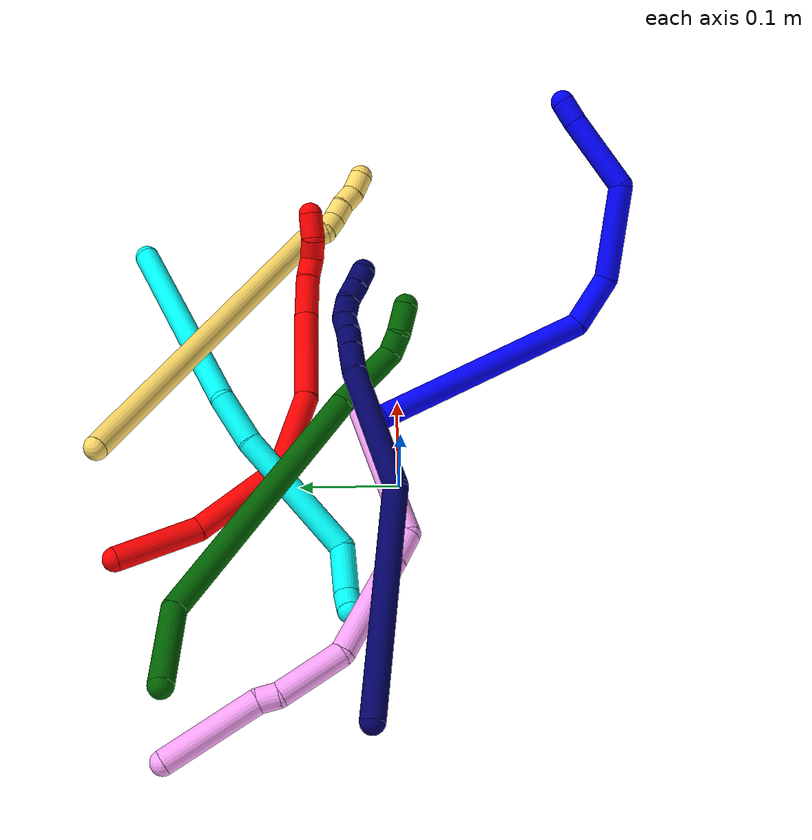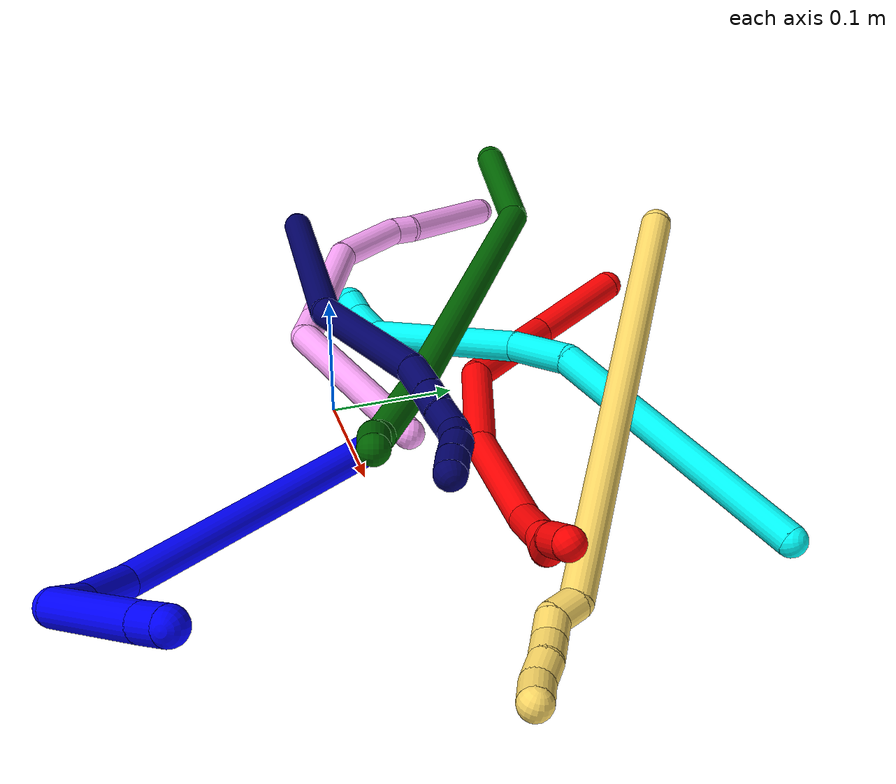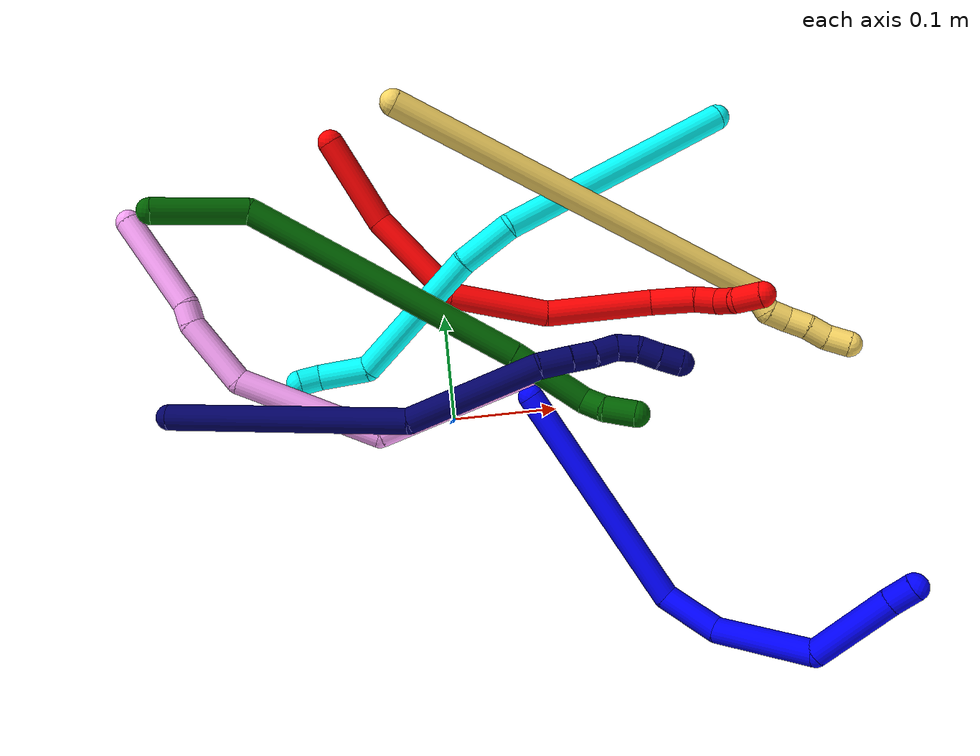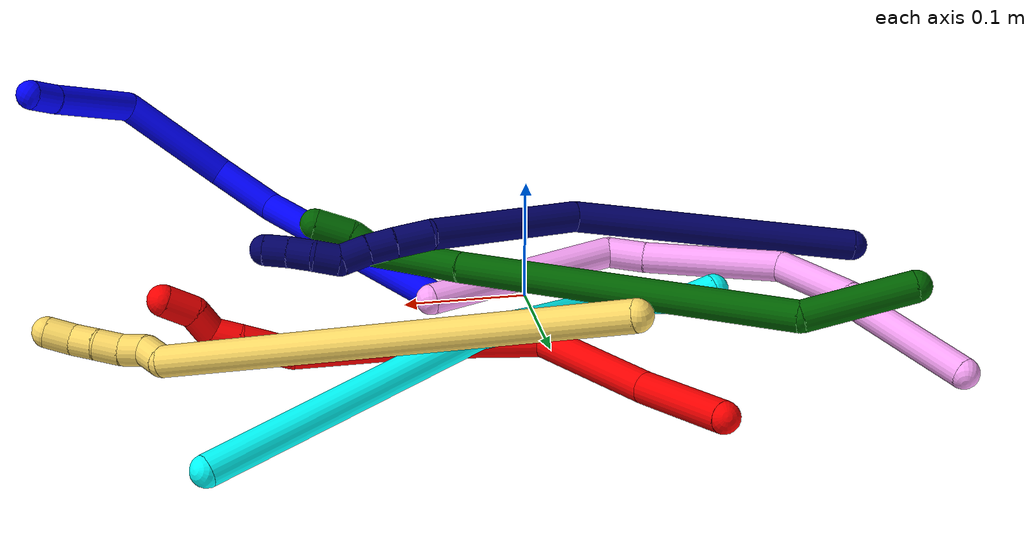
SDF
<sdf version="1.7">
 <world name="default">
  <plugin name="TubeGeneratorPlugin" filename="libtube_generator_plugin.so"/>
  <model name="photoneo_s_sensor">
   <static>1</static>
   <pose>0 0 2 1.57079 1.57079 3.14159</pose>
   <link name="link">
    <inertial><mass>0.1</mass></inertial>
    <sensor name="sensor" type="depth">
     <update_rate>30</update_rate>
     <camera>
      <horizontal_fov>1.22</horizontal_fov>
      <image><width>1920</width><height>1200</height><format>B8G8R8</format></image>
      <clip><near>0.1</near><far>4</far></clip>
      <depth_camera><output>points</output></depth_camera>
     </camera>
     <plugin name="camera_plugin" filename="libgazebo_ros_depth_camera.so">
      <baseline>0.2</baseline>
      <alwaysOn>1</alwaysOn>
      <updateRate>0.0</updateRate>
      <cameraName>camera_ir</cameraName>
      <imageTopicName>/camera/color/image_raw</imageTopicName>
      <cameraInfoTopicName>/camera/color/camera_info</cameraInfoTopicName>
      <depthImageTopicName>/camera/depth/image_raw</depthImageTopicName>
      <depthImageCameraInfoTopicName>/camera/depth/camera_info</depthImageCameraInfoTopicName>
      <pointCloudTopicName>/camera/depth/points</pointCloudTopicName>
      <frameName>fr_optical</frameName>
      <pointCloudCutoff>0.1</pointCloudCutoff>
      <pointCloudCutoffMax>2.0</pointCloudCutoffMax>
      <distortionK1>0</distortionK1>
      <distortionK2>0</distortionK2>
      <distortionK3>0</distortionK3>
      <distortionT1>0</distortionT1>
      <distortionT2>0</distortionT2>
      <CxPrime>0</CxPrime>
      <Cx>0</Cx>
      <Cy>0</Cy>
      <focalLength>0</focalLength>
      <hackBaseline>0</hackBaseline>
     </plugin>
    </sensor>
   </link>
  </model>
  <gravity>0 0 -9.8</gravity>
  <magnetic_field>6e-06 2.3e-05 -4.2e-05</magnetic_field>
  <atmosphere type="adiabatic"/>
  <physics name="default_physics" default="0" type="ode">
   <max_step_size>0.003</max_step_size>
   <real_time_factor>1</real_time_factor>
   <real_time_update_rate>1000</real_time_update_rate>
   <max_contacts>10000</max_contacts>
   <ode>
    <solver>
     <type>quick</type>
     <iters>100</iters>
     <sor>1.3</sor>
     <use_dynamic_moi_rescaling>0</use_dynamic_moi_rescaling>
    </solver>
    <constraints>
     <contact_max_correcting_vel>0</contact_max_correcting_vel>
     <contact_surface_layer>0.001</contact_surface_layer>
     <cfm>0</cfm>
     <erp>0.2</erp>
    </constraints>
   </ode>
  </physics>
  <scene><ambient>0.4 0.4 0.4 1</ambient><background>0.7 0.7 0.7 1</background><shadows>0</shadows></scene>
  <audio><device>default</device></audio>
  <spherical_coordinates>
   <surface_model>EARTH_WGS84</surface_model>
   <latitude_deg>0</latitude_deg>
   <longitude_deg>0</longitude_deg>
   <elevation>0</elevation>
   <heading_deg>0</heading_deg>
  </spherical_coordinates>
  <model name="bin">
   <static>1</static>
   <link name="bottom">
    <collision name="collision-bottom">
     <pose>0 0 -0.01 0 -0 0</pose>
     <geometry><box><size>0.8 0.6 0.02</size></box></geometry>
     <surface>
      <friction><ode><mu>100</mu><mu2>100</mu2></ode></friction>
      <contact><collide_bitmask>65535</collide_bitmask></contact>
     </surface>
    </collision>
   </link>
   <link name="west_wall">
    <collision name="collision-west_wall">
     <pose>-0.41 0 0.1 0 -0 0</pose>
     <geometry><box><size>0.02 0.6 0.2</size></box></geometry>
     <surface>
      <friction><ode><mu>100</mu><mu2>100</mu2></ode></friction>
      <contact><collide_bitmask>65535</collide_bitmask></contact>
     </surface>
    </collision>
   </link>
   <link name="east_wall">
    <collision name="collision-east_wall">
     <pose>0.41 0 0.1 0 -0 0</pose>
     <geometry><box><size>0.02 0.6 0.2</size></box></geometry>
     <surface>
      <friction><ode><mu>100</mu><mu2>100</mu2></ode></friction>
      <contact><collide_bitmask>65535</collide_bitmask></contact>
     </surface>
    </collision>
   </link>
   <link name="south_wall">
    <collision name="collision-south_wall">
     <pose>0 -0.31 0.1 0 -0 0</pose>
     <geometry><box><size>0.8 0.02 0.2</size></box></geometry>
     <surface>
      <friction><ode><mu>100</mu><mu2>100</mu2></ode></friction>
      <contact><collide_bitmask>65535</collide_bitmask></contact>
     </surface>
    </collision>
   </link>
   <link name="north_wall">
    <collision name="collision-north_wall">
     <pose>0 0.31 0.1 0 -0 0</pose>
     <geometry><box><size>0.8 0.02 0.2</size></box></geometry>
     <surface>
      <friction><ode><mu>100</mu><mu2>100</mu2></ode></friction>
      <contact><collide_bitmask>65535</collide_bitmask></contact>
     </surface>
    </collision>
   </link>
  </model>
  <model name="1">
   <static>0</static>
   <link name="1">
    <collision name="collision-cylinder-e_1_1_4">
     <pose>0.036369 -0.067214 0.088964 0.647024 0.315301 0.106501</pose>
     <geometry><cylinder><radius>0.0125</radius><length>0.234564</length></cylinder></geometry>
     <surface>
      <friction><ode><mu>1.16</mu><mu2>1.16</mu2><slip1>0</slip1><slip2>0</slip2></ode></friction>
      <contact><ode><kp>1e+06</kp><kd>1</kd><max_vel>0</max_vel><min_depth>0.001</min_depth></ode></contact>
     </surface>
    </collision>
    <visual name="visual-cylinder-e_1_1_4">
     <pose>0.036369 -0.067214 0.088964 0.647024 0.315301 0.106501</pose>
     <geometry><cylinder><radius>0.0125</radius><length>0.234564</length></cylinder></geometry>
     <material><ambient>0 0 1 1</ambient></material>
    </visual>
    <collision name="collision-cylinder-e_2_4_5">
     <pose>0.072921 -0.138277 0.206439 0.134203 0.006327 0.000425</pose>
     <geometry><cylinder><radius>0.0125</radius><length>0.057541</length></cylinder></geometry>
     <surface>
      <friction><ode><mu>1.16</mu><mu2>1.16</mu2><slip1>0</slip1><slip2>0</slip2></ode></friction>
      <contact><ode><kp>1e+06</kp><kd>1</kd><max_vel>0</max_vel><min_depth>0.001</min_depth></ode></contact>
     </surface>
    </collision>
    <visual name="visual-cylinder-e_2_4_5">
     <pose>0.072921 -0.138277 0.206439 0.134203 0.006327 0.000425</pose>
     <geometry><cylinder><radius>0.0125</radius><length>0.057541</length></cylinder></geometry>
     <material><ambient>0 0 1 1</ambient></material>
    </visual>
    <collision name="collision-cylinder-e_3_5_6">
     <pose>0.063118 -0.129267 0.281799 -0.267893 -0.202698 0.027406</pose>
     <geometry><cylinder><radius>0.0125</radius><length>0.099194</length></cylinder></geometry>
     <surface>
      <friction><ode><mu>1.16</mu><mu2>1.16</mu2><slip1>0</slip1><slip2>0</slip2></ode></friction>
      <contact><ode><kp>1e+06</kp><kd>1</kd><max_vel>0</max_vel><min_depth>0.001</min_depth></ode></contact>
     </surface>
    </collision>
    <visual name="visual-cylinder-e_3_5_6">
     <pose>0.063118 -0.129267 0.281799 -0.267893 -0.202698 0.027406</pose>
     <geometry><cylinder><radius>0.0125</radius><length>0.099194</length></cylinder></geometry>
     <material><ambient>0 0 1 1</ambient></material>
    </visual>
    <collision name="collision-cylinder-e_4_6_7">
     <pose>0.050987 -0.080466 0.349741 -1.04008 -0.051474 0.029479</pose>
     <geometry><cylinder><radius>0.0125</radius><length>0.083457</length></cylinder></geometry>
     <surface>
      <friction><ode><mu>1.16</mu><mu2>1.16</mu2><slip1>0</slip1><slip2>0</slip2></ode></friction>
      <contact><ode><kp>1e+06</kp><kd>1</kd><max_vel>0</max_vel><min_depth>0.001</min_depth></ode></contact>
     </surface>
    </collision>
    <visual name="visual-cylinder-e_4_6_7">
     <pose>0.050987 -0.080466 0.349741 -1.04008 -0.051474 0.029479</pose>
     <geometry><cylinder><radius>0.0125</radius><length>0.083457</length></cylinder></geometry>
     <material><ambient>0 0 1 1</ambient></material>
    </visual>
    <collision name="collision-cylinder-e_5_7_2">
     <pose>0.047685 -0.034102 0.377858 -0.977823 -0.091643 0.048778</pose>
     <geometry><cylinder><radius>0.0125</radius><length>0.025244</length></cylinder></geometry>
     <surface>
      <friction><ode><mu>1.16</mu><mu2>1.16</mu2><slip1>0</slip1><slip2>0</slip2></ode></friction>
      <contact><ode><kp>1e+06</kp><kd>1</kd><max_vel>0</max_vel><min_depth>0.001</min_depth></ode></contact>
     </surface>
    </collision>
    <visual name="visual-cylinder-e_5_7_2">
     <pose>0.047685 -0.034102 0.377858 -0.977823 -0.091643 0.048778</pose>
     <geometry><cylinder><radius>0.0125</radius><length>0.025244</length></cylinder></geometry>
     <material><ambient>0 0 1 1</ambient></material>
    </visual>
    <collision name="collision-sphere-2">
     <pose>0.04653 -0.023679 0.384882 0 -0 0</pose>
     <geometry><sphere><radius>0.0125</radius></sphere></geometry>
     <surface>
      <friction><ode><mu>1.16</mu><mu2>1.16</mu2><slip1>0</slip1><slip2>0</slip2></ode></friction>
      <contact><ode><kp>1e+06</kp><kd>1</kd><max_vel>0</max_vel><min_depth>0.001</min_depth></ode></contact>
     </surface>
    </collision>
    <visual name="visual-sphere-2">
     <pose>0.04653 -0.023679 0.384882 0 -0 0</pose>
     <geometry><sphere><radius>0.0125</radius></sphere></geometry>
     <material><ambient>0 0 1 1</ambient></material>
    </visual>
    <collision name="collision-sphere-7">
     <pose>0.04884 -0.044526 0.370834 0 -0 0</pose>
     <geometry><sphere><radius>0.0125</radius></sphere></geometry>
     <surface>
      <friction><ode><mu>1.16</mu><mu2>1.16</mu2><slip1>0</slip1><slip2>0</slip2></ode></friction>
      <contact><ode><kp>1e+06</kp><kd>1</kd><max_vel>0</max_vel><min_depth>0.001</min_depth></ode></contact>
     </surface>
    </collision>
    <visual name="visual-sphere-7">
     <pose>0.04884 -0.044526 0.370834 0 -0 0</pose>
     <geometry><sphere><radius>0.0125</radius></sphere></geometry>
     <material><ambient>0 0 1 1</ambient></material>
    </visual>
    <collision name="collision-sphere-6">
     <pose>0.053134 -0.116407 0.328648 0 -0 0</pose>
     <geometry><sphere><radius>0.0125</radius></sphere></geometry>
     <surface>
      <friction><ode><mu>1.16</mu><mu2>1.16</mu2><slip1>0</slip1><slip2>0</slip2></ode></friction>
      <contact><ode><kp>1e+06</kp><kd>1</kd><max_vel>0</max_vel><min_depth>0.001</min_depth></ode></contact>
     </surface>
    </collision>
    <visual name="visual-sphere-6">
     <pose>0.053134 -0.116407 0.328648 0 -0 0</pose>
     <geometry><sphere><radius>0.0125</radius></sphere></geometry>
     <material><ambient>0 0 1 1</ambient></material>
    </visual>
    <collision name="collision-sphere-5">
     <pose>0.073103 -0.142127 0.23495 0 -0 0</pose>
     <geometry><sphere><radius>0.0125</radius></sphere></geometry>
     <surface>
      <friction><ode><mu>1.16</mu><mu2>1.16</mu2><slip1>0</slip1><slip2>0</slip2></ode></friction>
      <contact><ode><kp>1e+06</kp><kd>1</kd><max_vel>0</max_vel><min_depth>0.001</min_depth></ode></contact>
     </surface>
    </collision>
    <visual name="visual-sphere-5">
     <pose>0.073103 -0.142127 0.23495 0 -0 0</pose>
     <geometry><sphere><radius>0.0125</radius></sphere></geometry>
     <material><ambient>0 0 1 1</ambient></material>
    </visual>
    <collision name="collision-sphere-1">
     <geometry><sphere><radius>0.0125</radius></sphere></geometry>
     <surface>
      <friction><ode><mu>1.16</mu><mu2>1.16</mu2><slip1>0</slip1><slip2>0</slip2></ode></friction>
      <contact><ode><kp>1e+06</kp><kd>1</kd><max_vel>0</max_vel><min_depth>0.001</min_depth></ode></contact>
     </surface>
    </collision>
    <visual name="visual-sphere-1">
     <geometry><sphere><radius>0.0125</radius></sphere></geometry>
     <material><ambient>0 0 1 1</ambient></material>
    </visual>
    <collision name="collision-sphere-4">
     <pose>0.072739 -0.134428 0.177928 0 -0 0</pose>
     <geometry><sphere><radius>0.0125</radius></sphere></geometry>
     <surface>
      <friction><ode><mu>1.16</mu><mu2>1.16</mu2><slip1>0</slip1><slip2>0</slip2></ode></friction>
      <contact><ode><kp>1e+06</kp><kd>1</kd><max_vel>0</max_vel><min_depth>0.001</min_depth></ode></contact>
     </surface>
    </collision>
    <visual name="visual-sphere-4">
     <pose>0.072739 -0.134428 0.177928 0 -0 0</pose>
     <geometry><sphere><radius>0.0125</radius></sphere></geometry>
     <material><ambient>0 0 1 1</ambient></material>
    </visual>
    <inertial>
     <pose>0.048894 -0.088243 0.198853 0 -0 0</pose>
     <mass>0.5</mass>
     <inertia>
      <ixx>0.001298</ixx>
      <ixy>0</ixy>
      <ixz>0</ixz>
      <iyy>0.001122</iyy>
      <iyz>0</iyz>
      <izz>0.000269</izz>
     </inertia>
    </inertial>
   </link>
   <pose>0.076427 0.014571 0.011491 0.19685 1.10869 -0.287087</pose>
  </model>
  <model name="2">
   <static>0</static>
   <link name="2">
    <collision name="collision-cylinder-e_1_1_4">
     <pose>0.024966 -0.002267 0.036777 0.06156 0.595513 0.018897</pose>
     <geometry><cylinder><radius>0.0125</radius><length>0.089017</length></cylinder></geometry>
     <surface>
      <friction><ode><mu>1.16</mu><mu2>1.16</mu2><slip1>0</slip1><slip2>0</slip2></ode></friction>
      <contact><ode><kp>1e+06</kp><kd>1</kd><max_vel>0</max_vel><min_depth>0.001</min_depth></ode></contact>
     </surface>
    </collision>
    <visual name="visual-cylinder-e_1_1_4">
     <pose>0.024966 -0.002267 0.036777 0.06156 0.595513 0.018897</pose>
     <geometry><cylinder><radius>0.0125</radius><length>0.089017</length></cylinder></geometry>
     <material><ambient>1 0 0 1</ambient></material>
    </visual>
    <collision name="collision-cylinder-e_2_4_5">
     <pose>0.08892 -0.007148 0.105254 0.082288 0.886461 0.039082</pose>
     <geometry><cylinder><radius>0.0125</radius><length>0.100633</length></cylinder></geometry>
     <surface>
      <friction><ode><mu>1.16</mu><mu2>1.16</mu2><slip1>0</slip1><slip2>0</slip2></ode></friction>
      <contact><ode><kp>1e+06</kp><kd>1</kd><max_vel>0</max_vel><min_depth>0.001</min_depth></ode></contact>
     </surface>
    </collision>
    <visual name="visual-cylinder-e_2_4_5">
     <pose>0.08892 -0.007148 0.105254 0.082288 0.886461 0.039082</pose>
     <geometry><cylinder><radius>0.0125</radius><length>0.100633</length></cylinder></geometry>
     <material><ambient>1 0 0 1</ambient></material>
    </visual>
    <collision name="collision-cylinder-e_3_5_6">
     <pose>0.166221 -0.034904 0.148028 1.15593 0.948741 0.646361</pose>
     <geometry><cylinder><radius>0.0125</radius><length>0.09429</length></cylinder></geometry>
     <surface>
      <friction><ode><mu>1.16</mu><mu2>1.16</mu2><slip1>0</slip1><slip2>0</slip2></ode></friction>
      <contact><ode><kp>1e+06</kp><kd>1</kd><max_vel>0</max_vel><min_depth>0.001</min_depth></ode></contact>
     </surface>
    </collision>
    <visual name="visual-cylinder-e_3_5_6">
     <pose>0.166221 -0.034904 0.148028 1.15593 0.948741 0.646361</pose>
     <geometry><cylinder><radius>0.0125</radius><length>0.09429</length></cylinder></geometry>
     <material><ambient>1 0 0 1</ambient></material>
    </visual>
    <collision name="collision-cylinder-e_4_6_7">
     <pose>0.244796 -0.09122 0.156546 1.65256 0.910291 0.976531</pose>
     <geometry><cylinder><radius>0.0125</radius><length>0.101968</length></cylinder></geometry>
     <surface>
      <friction><ode><mu>1.16</mu><mu2>1.16</mu2><slip1>0</slip1><slip2>0</slip2></ode></friction>
      <contact><ode><kp>1e+06</kp><kd>1</kd><max_vel>0</max_vel><min_depth>0.001</min_depth></ode></contact>
     </surface>
    </collision>
    <visual name="visual-cylinder-e_4_6_7">
     <pose>0.244796 -0.09122 0.156546 1.65256 0.910291 0.976531</pose>
     <geometry><cylinder><radius>0.0125</radius><length>0.101968</length></cylinder></geometry>
     <material><ambient>1 0 0 1</ambient></material>
    </visual>
    <collision name="collision-cylinder-e_5_7_8">
     <pose>0.30509 -0.129351 0.150523 2.03339 1.20068 1.67179</pose>
     <geometry><cylinder><radius>0.0125</radius><length>0.042974</length></cylinder></geometry>
     <surface>
      <friction><ode><mu>1.16</mu><mu2>1.16</mu2><slip1>0</slip1><slip2>0</slip2></ode></friction>
      <contact><ode><kp>1e+06</kp><kd>1</kd><max_vel>0</max_vel><min_depth>0.001</min_depth></ode></contact>
     </surface>
    </collision>
    <visual name="visual-cylinder-e_5_7_8">
     <pose>0.30509 -0.129351 0.150523 2.03339 1.20068 1.67179</pose>
     <geometry><cylinder><radius>0.0125</radius><length>0.042974</length></cylinder></geometry>
     <material><ambient>1 0 0 1</ambient></material>
    </visual>
    <collision name="collision-cylinder-e_6_8_9">
     <pose>0.335586 -0.13997 0.147224 1.52445 1.23375 1.19034</pose>
     <geometry><cylinder><radius>0.0125</radius><length>0.022177</length></cylinder></geometry>
     <surface>
      <friction><ode><mu>1.16</mu><mu2>1.16</mu2><slip1>0</slip1><slip2>0</slip2></ode></friction>
      <contact><ode><kp>1e+06</kp><kd>1</kd><max_vel>0</max_vel><min_depth>0.001</min_depth></ode></contact>
     </surface>
    </collision>
    <visual name="visual-cylinder-e_6_8_9">
     <pose>0.335586 -0.13997 0.147224 1.52445 1.23375 1.19034</pose>
     <geometry><cylinder><radius>0.0125</radius><length>0.022177</length></cylinder></geometry>
     <material><ambient>1 0 0 1</ambient></material>
    </visual>
    <collision name="collision-cylinder-e_7_9_10">
     <pose>0.356079 -0.140766 0.14338 -2.52141 1.1137 -2.19094</pose>
     <geometry><cylinder><radius>0.0125</radius><length>0.022351</length></cylinder></geometry>
     <surface>
      <friction><ode><mu>1.16</mu><mu2>1.16</mu2><slip1>0</slip1><slip2>0</slip2></ode></friction>
      <contact><ode><kp>1e+06</kp><kd>1</kd><max_vel>0</max_vel><min_depth>0.001</min_depth></ode></contact>
     </surface>
    </collision>
    <visual name="visual-cylinder-e_7_9_10">
     <pose>0.356079 -0.140766 0.14338 -2.52141 1.1137 -2.19094</pose>
     <geometry><cylinder><radius>0.0125</radius><length>0.022351</length></cylinder></geometry>
     <material><ambient>1 0 0 1</ambient></material>
    </visual>
    <collision name="collision-cylinder-e_8_10_2">
     <pose>0.378188 -0.140845 0.134662 2.58224 1.14006 2.29913</pose>
     <geometry><cylinder><radius>0.0125</radius><length>0.02659</length></cylinder></geometry>
     <surface>
      <friction><ode><mu>1.16</mu><mu2>1.16</mu2><slip1>0</slip1><slip2>0</slip2></ode></friction>
      <contact><ode><kp>1e+06</kp><kd>1</kd><max_vel>0</max_vel><min_depth>0.001</min_depth></ode></contact>
     </surface>
    </collision>
    <visual name="visual-cylinder-e_8_10_2">
     <pose>0.378188 -0.140845 0.134662 2.58224 1.14006 2.29913</pose>
     <geometry><cylinder><radius>0.0125</radius><length>0.02659</length></cylinder></geometry>
     <material><ambient>1 0 0 1</ambient></material>
    </visual>
    <collision name="collision-sphere-2">
     <pose>0.390268 -0.143791 0.129957 0 -0 0</pose>
     <geometry><sphere><radius>0.0125</radius></sphere></geometry>
     <surface>
      <friction><ode><mu>1.16</mu><mu2>1.16</mu2><slip1>0</slip1><slip2>0</slip2></ode></friction>
      <contact><ode><kp>1e+06</kp><kd>1</kd><max_vel>0</max_vel><min_depth>0.001</min_depth></ode></contact>
     </surface>
    </collision>
    <visual name="visual-sphere-2">
     <pose>0.390268 -0.143791 0.129957 0 -0 0</pose>
     <geometry><sphere><radius>0.0125</radius></sphere></geometry>
     <material><ambient>1 0 0 1</ambient></material>
    </visual>
    <collision name="collision-sphere-10">
     <pose>0.366107 -0.1379 0.139367 0 -0 0</pose>
     <geometry><sphere><radius>0.0125</radius></sphere></geometry>
     <surface>
      <friction><ode><mu>1.16</mu><mu2>1.16</mu2><slip1>0</slip1><slip2>0</slip2></ode></friction>
      <contact><ode><kp>1e+06</kp><kd>1</kd><max_vel>0</max_vel><min_depth>0.001</min_depth></ode></contact>
     </surface>
    </collision>
    <visual name="visual-sphere-10">
     <pose>0.366107 -0.1379 0.139367 0 -0 0</pose>
     <geometry><sphere><radius>0.0125</radius></sphere></geometry>
     <material><ambient>1 0 0 1</ambient></material>
    </visual>
    <collision name="collision-sphere-9">
     <pose>0.346051 -0.143633 0.147394 0 -0 0</pose>
     <geometry><sphere><radius>0.0125</radius></sphere></geometry>
     <surface>
      <friction><ode><mu>1.16</mu><mu2>1.16</mu2><slip1>0</slip1><slip2>0</slip2></ode></friction>
      <contact><ode><kp>1e+06</kp><kd>1</kd><max_vel>0</max_vel><min_depth>0.001</min_depth></ode></contact>
     </surface>
    </collision>
    <visual name="visual-sphere-9">
     <pose>0.346051 -0.143633 0.147394 0 -0 0</pose>
     <geometry><sphere><radius>0.0125</radius></sphere></geometry>
     <material><ambient>1 0 0 1</ambient></material>
    </visual>
    <collision name="collision-sphere-4">
     <pose>0.049932 -0.004534 0.073554 0 -0 0</pose>
     <geometry><sphere><radius>0.0125</radius></sphere></geometry>
     <surface>
      <friction><ode><mu>1.16</mu><mu2>1.16</mu2><slip1>0</slip1><slip2>0</slip2></ode></friction>
      <contact><ode><kp>1e+06</kp><kd>1</kd><max_vel>0</max_vel><min_depth>0.001</min_depth></ode></contact>
     </surface>
    </collision>
    <visual name="visual-sphere-4">
     <pose>0.049932 -0.004534 0.073554 0 -0 0</pose>
     <geometry><sphere><radius>0.0125</radius></sphere></geometry>
     <material><ambient>1 0 0 1</ambient></material>
    </visual>
    <collision name="collision-sphere-1">
     <geometry><sphere><radius>0.0125</radius></sphere></geometry>
     <surface>
      <friction><ode><mu>1.16</mu><mu2>1.16</mu2><slip1>0</slip1><slip2>0</slip2></ode></friction>
      <contact><ode><kp>1e+06</kp><kd>1</kd><max_vel>0</max_vel><min_depth>0.001</min_depth></ode></contact>
     </surface>
    </collision>
    <visual name="visual-sphere-1">
     <geometry><sphere><radius>0.0125</radius></sphere></geometry>
     <material><ambient>1 0 0 1</ambient></material>
    </visual>
    <collision name="collision-sphere-8">
     <pose>0.325121 -0.136306 0.147054 0 -0 0</pose>
     <geometry><sphere><radius>0.0125</radius></sphere></geometry>
     <surface>
      <friction><ode><mu>1.16</mu><mu2>1.16</mu2><slip1>0</slip1><slip2>0</slip2></ode></friction>
      <contact><ode><kp>1e+06</kp><kd>1</kd><max_vel>0</max_vel><min_depth>0.001</min_depth></ode></contact>
     </surface>
    </collision>
    <visual name="visual-sphere-8">
     <pose>0.325121 -0.136306 0.147054 0 -0 0</pose>
     <geometry><sphere><radius>0.0125</radius></sphere></geometry>
     <material><ambient>1 0 0 1</ambient></material>
    </visual>
    <collision name="collision-sphere-5">
     <pose>0.127907 -0.009763 0.136955 0 -0 0</pose>
     <geometry><sphere><radius>0.0125</radius></sphere></geometry>
     <surface>
      <friction><ode><mu>1.16</mu><mu2>1.16</mu2><slip1>0</slip1><slip2>0</slip2></ode></friction>
      <contact><ode><kp>1e+06</kp><kd>1</kd><max_vel>0</max_vel><min_depth>0.001</min_depth></ode></contact>
     </surface>
    </collision>
    <visual name="visual-sphere-5">
     <pose>0.127907 -0.009763 0.136955 0 -0 0</pose>
     <geometry><sphere><radius>0.0125</radius></sphere></geometry>
     <material><ambient>1 0 0 1</ambient></material>
    </visual>
    <collision name="collision-sphere-6">
     <pose>0.204535 -0.060045 0.159101 0 -0 0</pose>
     <geometry><sphere><radius>0.0125</radius></sphere></geometry>
     <surface>
      <friction><ode><mu>1.16</mu><mu2>1.16</mu2><slip1>0</slip1><slip2>0</slip2></ode></friction>
      <contact><ode><kp>1e+06</kp><kd>1</kd><max_vel>0</max_vel><min_depth>0.001</min_depth></ode></contact>
     </surface>
    </collision>
    <visual name="visual-sphere-6">
     <pose>0.204535 -0.060045 0.159101 0 -0 0</pose>
     <geometry><sphere><radius>0.0125</radius></sphere></geometry>
     <material><ambient>1 0 0 1</ambient></material>
    </visual>
    <collision name="collision-sphere-7">
     <pose>0.285058 -0.122396 0.153992 0 -0 0</pose>
     <geometry><sphere><radius>0.0125</radius></sphere></geometry>
     <surface>
      <friction><ode><mu>1.16</mu><mu2>1.16</mu2><slip1>0</slip1><slip2>0</slip2></ode></friction>
      <contact><ode><kp>1e+06</kp><kd>1</kd><max_vel>0</max_vel><min_depth>0.001</min_depth></ode></contact>
     </surface>
    </collision>
    <visual name="visual-sphere-7">
     <pose>0.285058 -0.122396 0.153992 0 -0 0</pose>
     <geometry><sphere><radius>0.0125</radius></sphere></geometry>
     <material><ambient>1 0 0 1</ambient></material>
    </visual>
    <inertial>
     <pose>0.180746 -0.058136 0.12061 0 -0 0</pose>
     <mass>0.5</mass>
     <inertia>
      <ixx>0.000282</ixx>
      <ixy>0</ixy>
      <ixz>0</ixz>
      <iyy>0.000345</iyy>
      <iyz>0</iyz>
      <izz>-0.000133</izz>
     </inertia>
    </inertial>
   </link>
   <pose>-0.090837 0.277826 0.024093 2.16811 -0.5464 -0.389938</pose>
  </model>
  <model name="3">
   <static>0</static>
   <link name="3">
    <collision name="collision-cylinder-e_1_1_4">
     <pose>-0.061755 -0.039916 -0.091901 2.73184 -0.552353 -1.87631</pose>
     <geometry><cylinder><radius>0.0125</radius><length>0.235395</length></cylinder></geometry>
     <surface>
      <friction><ode><mu>1.16</mu><mu2>1.16</mu2><slip1>0</slip1><slip2>0</slip2></ode></friction>
      <contact><ode><kp>1e+06</kp><kd>1</kd><max_vel>0</max_vel><min_depth>0.001</min_depth></ode></contact>
     </surface>
    </collision>
    <visual name="visual-cylinder-e_1_1_4">
     <pose>-0.061755 -0.039916 -0.091901 2.73184 -0.552353 -1.87631</pose>
     <geometry><cylinder><radius>0.0125</radius><length>0.235395</length></cylinder></geometry>
     <material><ambient>0.003922 1 0.996078 1</ambient></material>
    </visual>
    <collision name="collision-cylinder-e_2_4_5">
     <pose>-0.129734 -0.084429 -0.209831 2.96679 -0.231257 -1.84893</pose>
     <geometry><cylinder><radius>0.0125</radius><length>0.05431</length></cylinder></geometry>
     <surface>
      <friction><ode><mu>1.16</mu><mu2>1.16</mu2><slip1>0</slip1><slip2>0</slip2></ode></friction>
      <contact><ode><kp>1e+06</kp><kd>1</kd><max_vel>0</max_vel><min_depth>0.001</min_depth></ode></contact>
     </surface>
    </collision>
    <visual name="visual-cylinder-e_2_4_5">
     <pose>-0.129734 -0.084429 -0.209831 2.96679 -0.231257 -1.84893</pose>
     <geometry><cylinder><radius>0.0125</radius><length>0.05431</length></cylinder></geometry>
     <material><ambient>0.003922 1 0.996078 1</ambient></material>
    </visual>
    <collision name="collision-cylinder-e_3_5_6">
     <pose>-0.14028 -0.104878 -0.304176 2.91359 -0.061549 -0.525304</pose>
     <geometry><cylinder><radius>0.0125</radius><length>0.140527</length></cylinder></geometry>
     <surface>
      <friction><ode><mu>1.16</mu><mu2>1.16</mu2><slip1>0</slip1><slip2>0</slip2></ode></friction>
      <contact><ode><kp>1e+06</kp><kd>1</kd><max_vel>0</max_vel><min_depth>0.001</min_depth></ode></contact>
     </surface>
    </collision>
    <visual name="visual-cylinder-e_3_5_6">
     <pose>-0.14028 -0.104878 -0.304176 2.91359 -0.061549 -0.525304</pose>
     <geometry><cylinder><radius>0.0125</radius><length>0.140527</length></cylinder></geometry>
     <material><ambient>0.003922 1 0.996078 1</ambient></material>
    </visual>
    <collision name="collision-cylinder-e_4_6_7">
     <pose>-0.158364 -0.11792 -0.392237 -3.00028 -0.604012 2.69482</pose>
     <geometry><cylinder><radius>0.0125</radius><length>0.048465</length></cylinder></geometry>
     <surface>
      <friction><ode><mu>1.16</mu><mu2>1.16</mu2><slip1>0</slip1><slip2>0</slip2></ode></friction>
      <contact><ode><kp>1e+06</kp><kd>1</kd><max_vel>0</max_vel><min_depth>0.001</min_depth></ode></contact>
     </surface>
    </collision>
    <visual name="visual-cylinder-e_4_6_7">
     <pose>-0.158364 -0.11792 -0.392237 -3.00028 -0.604012 2.69482</pose>
     <geometry><cylinder><radius>0.0125</radius><length>0.048465</length></cylinder></geometry>
     <material><ambient>0.003922 1 0.996078 1</ambient></material>
    </visual>
    <collision name="collision-cylinder-e_5_7_2">
     <pose>-0.17966 -0.117592 -0.419094 2.80598 -0.785492 -2.36526</pose>
     <geometry><cylinder><radius>0.0125</radius><length>0.021303</length></cylinder></geometry>
     <surface>
      <friction><ode><mu>1.16</mu><mu2>1.16</mu2><slip1>0</slip1><slip2>0</slip2></ode></friction>
      <contact><ode><kp>1e+06</kp><kd>1</kd><max_vel>0</max_vel><min_depth>0.001</min_depth></ode></contact>
     </surface>
    </collision>
    <visual name="visual-cylinder-e_5_7_2">
     <pose>-0.17966 -0.117592 -0.419094 2.80598 -0.785492 -2.36526</pose>
     <geometry><cylinder><radius>0.0125</radius><length>0.021303</length></cylinder></geometry>
     <material><ambient>0.003922 1 0.996078 1</ambient></material>
    </visual>
    <collision name="collision-sphere-2">
     <pose>-0.187192 -0.120072 -0.426205 0 -0 0</pose>
     <geometry><sphere><radius>0.0125</radius></sphere></geometry>
     <surface>
      <friction><ode><mu>1.16</mu><mu2>1.16</mu2><slip1>0</slip1><slip2>0</slip2></ode></friction>
      <contact><ode><kp>1e+06</kp><kd>1</kd><max_vel>0</max_vel><min_depth>0.001</min_depth></ode></contact>
     </surface>
    </collision>
    <visual name="visual-sphere-2">
     <pose>-0.187192 -0.120072 -0.426205 0 -0 0</pose>
     <geometry><sphere><radius>0.0125</radius></sphere></geometry>
     <material><ambient>0.003922 1 0.996078 1</ambient></material>
    </visual>
    <collision name="collision-sphere-7">
     <pose>-0.172127 -0.115111 -0.411983 0 -0 0</pose>
     <geometry><sphere><radius>0.0125</radius></sphere></geometry>
     <surface>
      <friction><ode><mu>1.16</mu><mu2>1.16</mu2><slip1>0</slip1><slip2>0</slip2></ode></friction>
      <contact><ode><kp>1e+06</kp><kd>1</kd><max_vel>0</max_vel><min_depth>0.001</min_depth></ode></contact>
     </surface>
    </collision>
    <visual name="visual-sphere-7">
     <pose>-0.172127 -0.115111 -0.411983 0 -0 0</pose>
     <geometry><sphere><radius>0.0125</radius></sphere></geometry>
     <material><ambient>0.003922 1 0.996078 1</ambient></material>
    </visual>
    <collision name="collision-sphere-6">
     <pose>-0.144602 -0.12073 -0.372491 0 -0 0</pose>
     <geometry><sphere><radius>0.0125</radius></sphere></geometry>
     <surface>
      <friction><ode><mu>1.16</mu><mu2>1.16</mu2><slip1>0</slip1><slip2>0</slip2></ode></friction>
      <contact><ode><kp>1e+06</kp><kd>1</kd><max_vel>0</max_vel><min_depth>0.001</min_depth></ode></contact>
     </surface>
    </collision>
    <visual name="visual-sphere-6">
     <pose>-0.144602 -0.12073 -0.372491 0 -0 0</pose>
     <geometry><sphere><radius>0.0125</radius></sphere></geometry>
     <material><ambient>0.003922 1 0.996078 1</ambient></material>
    </visual>
    <collision name="collision-sphere-5">
     <pose>-0.135958 -0.089026 -0.23586 0 -0 0</pose>
     <geometry><sphere><radius>0.0125</radius></sphere></geometry>
     <surface>
      <friction><ode><mu>1.16</mu><mu2>1.16</mu2><slip1>0</slip1><slip2>0</slip2></ode></friction>
      <contact><ode><kp>1e+06</kp><kd>1</kd><max_vel>0</max_vel><min_depth>0.001</min_depth></ode></contact>
     </surface>
    </collision>
    <visual name="visual-sphere-5">
     <pose>-0.135958 -0.089026 -0.23586 0 -0 0</pose>
     <geometry><sphere><radius>0.0125</radius></sphere></geometry>
     <material><ambient>0.003922 1 0.996078 1</ambient></material>
    </visual>
    <collision name="collision-sphere-1">
     <geometry><sphere><radius>0.0125</radius></sphere></geometry>
     <surface>
      <friction><ode><mu>1.16</mu><mu2>1.16</mu2><slip1>0</slip1><slip2>0</slip2></ode></friction>
      <contact><ode><kp>1e+06</kp><kd>1</kd><max_vel>0</max_vel><min_depth>0.001</min_depth></ode></contact>
     </surface>
    </collision>
    <visual name="visual-sphere-1">
     <geometry><sphere><radius>0.0125</radius></sphere></geometry>
     <material><ambient>0.003922 1 0.996078 1</ambient></material>
    </visual>
    <collision name="collision-sphere-4">
     <pose>-0.12351 -0.079832 -0.183801 0 -0 0</pose>
     <geometry><sphere><radius>0.0125</radius></sphere></geometry>
     <surface>
      <friction><ode><mu>1.16</mu><mu2>1.16</mu2><slip1>0</slip1><slip2>0</slip2></ode></friction>
      <contact><ode><kp>1e+06</kp><kd>1</kd><max_vel>0</max_vel><min_depth>0.001</min_depth></ode></contact>
     </surface>
    </collision>
    <visual name="visual-sphere-4">
     <pose>-0.12351 -0.079832 -0.183801 0 -0 0</pose>
     <geometry><sphere><radius>0.0125</radius></sphere></geometry>
     <material><ambient>0.003922 1 0.996078 1</ambient></material>
    </visual>
    <inertial>
     <pose>-0.105596 -0.073879 -0.207423 0 -0 0</pose>
     <mass>0.5</mass>
     <inertia>
      <ixx>-0.001124</ixx>
      <ixy>0</ixy>
      <ixz>0</ixz>
      <iyy>-0.000689</iyy>
      <iyz>0</iyz>
      <izz>0.000994</izz>
     </inertia>
    </inertial>
   </link>
   <pose>0.283767 0.266514 0.011753 -1.04682 0.552618 -0.637703</pose>
  </model>
  <model name="4">
   <static>0</static>
   <link name="4">
    <collision name="collision-cylinder-e_1_1_4">
     <pose>-0.022665 0.070218 -0.03439 -2.02622 -0.282144 0.447739</pose>
     <geometry><cylinder><radius>0.0125</radius><length>0.162811</length></cylinder></geometry>
     <surface>
      <friction><ode><mu>1.16</mu><mu2>1.16</mu2><slip1>0</slip1><slip2>0</slip2></ode></friction>
      <contact><ode><kp>1e+06</kp><kd>1</kd><max_vel>0</max_vel><min_depth>0.001</min_depth></ode></contact>
     </surface>
    </collision>
    <visual name="visual-cylinder-e_1_1_4">
     <pose>-0.022665 0.070218 -0.03439 -2.02622 -0.282144 0.447739</pose>
     <geometry><cylinder><radius>0.0125</radius><length>0.162811</length></cylinder></geometry>
     <material><ambient>1 0.65098 0.996078 1</ambient></material>
    </visual>
    <collision name="collision-cylinder-e_2_4_5">
     <pose>-0.052499 0.153753 -0.064128 -1.23476 -0.470219 0.336903</pose>
     <geometry><cylinder><radius>0.0125</radius><length>0.031648</length></cylinder></geometry>
     <surface>
      <friction><ode><mu>1.16</mu><mu2>1.16</mu2><slip1>0</slip1><slip2>0</slip2></ode></friction>
      <contact><ode><kp>1e+06</kp><kd>1</kd><max_vel>0</max_vel><min_depth>0.001</min_depth></ode></contact>
     </surface>
    </collision>
    <visual name="visual-cylinder-e_2_4_5">
     <pose>-0.052499 0.153753 -0.064128 -1.23476 -0.470219 0.336903</pose>
     <geometry><cylinder><radius>0.0125</radius><length>0.031648</length></cylinder></geometry>
     <material><ambient>1 0.65098 0.996078 1</ambient></material>
    </visual>
    <collision name="collision-cylinder-e_3_5_6">
     <pose>-0.089086 0.212384 -0.044056 -1.24279 -0.551082 0.399483</pose>
     <geometry><cylinder><radius>0.0125</radius><length>0.112367</length></cylinder></geometry>
     <surface>
      <friction><ode><mu>1.16</mu><mu2>1.16</mu2><slip1>0</slip1><slip2>0</slip2></ode></friction>
      <contact><ode><kp>1e+06</kp><kd>1</kd><max_vel>0</max_vel><min_depth>0.001</min_depth></ode></contact>
     </surface>
    </collision>
    <visual name="visual-cylinder-e_3_5_6">
     <pose>-0.089086 0.212384 -0.044056 -1.24279 -0.551082 0.399483</pose>
     <geometry><cylinder><radius>0.0125</radius><length>0.112367</length></cylinder></geometry>
     <material><ambient>1 0.65098 0.996078 1</ambient></material>
    </visual>
    <collision name="collision-cylinder-e_4_6_7">
     <pose>-0.134336 0.276962 -0.003679 -0.65736 -0.465383 0.161297</pose>
     <geometry><cylinder><radius>0.0125</radius><length>0.070555</length></cylinder></geometry>
     <surface>
      <friction><ode><mu>1.16</mu><mu2>1.16</mu2><slip1>0</slip1><slip2>0</slip2></ode></friction>
      <contact><ode><kp>1e+06</kp><kd>1</kd><max_vel>0</max_vel><min_depth>0.001</min_depth></ode></contact>
     </surface>
    </collision>
    <visual name="visual-cylinder-e_4_6_7">
     <pose>-0.134336 0.276962 -0.003679 -0.65736 -0.465383 0.161297</pose>
     <geometry><cylinder><radius>0.0125</radius><length>0.070555</length></cylinder></geometry>
     <material><ambient>1 0.65098 0.996078 1</ambient></material>
    </visual>
    <collision name="collision-cylinder-e_5_7_8">
     <pose>-0.153499 0.298958 0.030549 -0.28664 -0.331931 0.048336</pose>
     <geometry><cylinder><radius>0.0125</radius><length>0.020451</length></cylinder></geometry>
     <surface>
      <friction><ode><mu>1.16</mu><mu2>1.16</mu2><slip1>0</slip1><slip2>0</slip2></ode></friction>
      <contact><ode><kp>1e+06</kp><kd>1</kd><max_vel>0</max_vel><min_depth>0.001</min_depth></ode></contact>
     </surface>
    </collision>
    <visual name="visual-cylinder-e_5_7_8">
     <pose>-0.153499 0.298958 0.030549 -0.28664 -0.331931 0.048336</pose>
     <geometry><cylinder><radius>0.0125</radius><length>0.020451</length></cylinder></geometry>
     <material><ambient>1 0.65098 0.996078 1</ambient></material>
    </visual>
    <collision name="collision-cylinder-e_6_8_2">
     <pose>-0.173662 0.329434 0.079277 -0.612838 -0.335749 0.107132</pose>
     <geometry><cylinder><radius>0.0125</radius><length>0.102169</length></cylinder></geometry>
     <surface>
      <friction><ode><mu>1.16</mu><mu2>1.16</mu2><slip1>0</slip1><slip2>0</slip2></ode></friction>
      <contact><ode><kp>1e+06</kp><kd>1</kd><max_vel>0</max_vel><min_depth>0.001</min_depth></ode></contact>
     </surface>
    </collision>
    <visual name="visual-cylinder-e_6_8_2">
     <pose>-0.173662 0.329434 0.079277 -0.612838 -0.335749 0.107132</pose>
     <geometry><cylinder><radius>0.0125</radius><length>0.102169</length></cylinder></geometry>
     <material><ambient>1 0.65098 0.996078 1</ambient></material>
    </visual>
    <collision name="collision-sphere-2">
     <pose>-0.190494 0.357176 0.118731 0 -0 0</pose>
     <geometry><sphere><radius>0.0125</radius></sphere></geometry>
     <surface>
      <friction><ode><mu>1.16</mu><mu2>1.16</mu2><slip1>0</slip1><slip2>0</slip2></ode></friction>
      <contact><ode><kp>1e+06</kp><kd>1</kd><max_vel>0</max_vel><min_depth>0.001</min_depth></ode></contact>
     </surface>
    </collision>
    <visual name="visual-sphere-2">
     <pose>-0.190494 0.357176 0.118731 0 -0 0</pose>
     <geometry><sphere><radius>0.0125</radius></sphere></geometry>
     <material><ambient>1 0.65098 0.996078 1</ambient></material>
    </visual>
    <collision name="collision-sphere-4">
     <pose>-0.045329 0.140435 -0.068779 0 -0 0</pose>
     <geometry><sphere><radius>0.0125</radius></sphere></geometry>
     <surface>
      <friction><ode><mu>1.16</mu><mu2>1.16</mu2><slip1>0</slip1><slip2>0</slip2></ode></friction>
      <contact><ode><kp>1e+06</kp><kd>1</kd><max_vel>0</max_vel><min_depth>0.001</min_depth></ode></contact>
     </surface>
    </collision>
    <visual name="visual-sphere-4">
     <pose>-0.045329 0.140435 -0.068779 0 -0 0</pose>
     <geometry><sphere><radius>0.0125</radius></sphere></geometry>
     <material><ambient>1 0.65098 0.996078 1</ambient></material>
    </visual>
    <collision name="collision-sphere-1">
     <geometry><sphere><radius>0.0125</radius></sphere></geometry>
     <surface>
      <friction><ode><mu>1.16</mu><mu2>1.16</mu2><slip1>0</slip1><slip2>0</slip2></ode></friction>
      <contact><ode><kp>1e+06</kp><kd>1</kd><max_vel>0</max_vel><min_depth>0.001</min_depth></ode></contact>
     </surface>
    </collision>
    <visual name="visual-sphere-1">
     <geometry><sphere><radius>0.0125</radius></sphere></geometry>
     <material><ambient>1 0.65098 0.996078 1</ambient></material>
    </visual>
    <collision name="collision-sphere-8">
     <pose>-0.156831 0.301691 0.039822 0 -0 0</pose>
     <geometry><sphere><radius>0.0125</radius></sphere></geometry>
     <surface>
      <friction><ode><mu>1.16</mu><mu2>1.16</mu2><slip1>0</slip1><slip2>0</slip2></ode></friction>
      <contact><ode><kp>1e+06</kp><kd>1</kd><max_vel>0</max_vel><min_depth>0.001</min_depth></ode></contact>
     </surface>
    </collision>
    <visual name="visual-sphere-8">
     <pose>-0.156831 0.301691 0.039822 0 -0 0</pose>
     <geometry><sphere><radius>0.0125</radius></sphere></geometry>
     <material><ambient>1 0.65098 0.996078 1</ambient></material>
    </visual>
    <collision name="collision-sphere-5">
     <pose>-0.059668 0.16707 -0.059476 0 -0 0</pose>
     <geometry><sphere><radius>0.0125</radius></sphere></geometry>
     <surface>
      <friction><ode><mu>1.16</mu><mu2>1.16</mu2><slip1>0</slip1><slip2>0</slip2></ode></friction>
      <contact><ode><kp>1e+06</kp><kd>1</kd><max_vel>0</max_vel><min_depth>0.001</min_depth></ode></contact>
     </surface>
    </collision>
    <visual name="visual-sphere-5">
     <pose>-0.059668 0.16707 -0.059476 0 -0 0</pose>
     <geometry><sphere><radius>0.0125</radius></sphere></geometry>
     <material><ambient>1 0.65098 0.996078 1</ambient></material>
    </visual>
    <collision name="collision-sphere-6">
     <pose>-0.118505 0.257699 -0.028635 0 -0 0</pose>
     <geometry><sphere><radius>0.0125</radius></sphere></geometry>
     <surface>
      <friction><ode><mu>1.16</mu><mu2>1.16</mu2><slip1>0</slip1><slip2>0</slip2></ode></friction>
      <contact><ode><kp>1e+06</kp><kd>1</kd><max_vel>0</max_vel><min_depth>0.001</min_depth></ode></contact>
     </surface>
    </collision>
    <visual name="visual-sphere-6">
     <pose>-0.118505 0.257699 -0.028635 0 -0 0</pose>
     <geometry><sphere><radius>0.0125</radius></sphere></geometry>
     <material><ambient>1 0.65098 0.996078 1</ambient></material>
    </visual>
    <collision name="collision-sphere-7">
     <pose>-0.150167 0.296225 0.021276 0 -0 0</pose>
     <geometry><sphere><radius>0.0125</radius></sphere></geometry>
     <surface>
      <friction><ode><mu>1.16</mu><mu2>1.16</mu2><slip1>0</slip1><slip2>0</slip2></ode></friction>
      <contact><ode><kp>1e+06</kp><kd>1</kd><max_vel>0</max_vel><min_depth>0.001</min_depth></ode></contact>
     </surface>
    </collision>
    <visual name="visual-sphere-7">
     <pose>-0.150167 0.296225 0.021276 0 -0 0</pose>
     <geometry><sphere><radius>0.0125</radius></sphere></geometry>
     <material><ambient>1 0.65098 0.996078 1</ambient></material>
    </visual>
    <inertial>
     <pose>-0.091444 0.198952 -0.008228 0 -0 0</pose>
     <mass>0.5</mass>
     <inertia>
      <ixx>0.000726</ixx>
      <ixy>0</ixy>
      <ixz>0</ixz>
      <iyy>0.000298</iyy>
      <iyz>0</iyz>
      <izz>-0.000264</izz>
     </inertia>
    </inertial>
   </link>
   <pose>0.084713 0.039985 0.022684 -2.27248 1.0482 -0.786511</pose>
  </model>
  <model name="5">
   <static>0</static>
   <link name="5">
    <collision name="collision-cylinder-e_1_1_4">
     <pose>0.178969 -0.033009 -0.07178 2.71057 1.15507 2.49342</pose>
     <geometry><cylinder><radius>0.0125</radius><length>0.391263</length></cylinder></geometry>
     <surface>
      <friction><ode><mu>1.16</mu><mu2>1.16</mu2><slip1>0</slip1><slip2>0</slip2></ode></friction>
      <contact><ode><kp>1e+06</kp><kd>1</kd><max_vel>0</max_vel><min_depth>0.001</min_depth></ode></contact>
     </surface>
    </collision>
    <visual name="visual-cylinder-e_1_1_4">
     <pose>0.178969 -0.033009 -0.07178 2.71057 1.15507 2.49342</pose>
     <geometry><cylinder><radius>0.0125</radius><length>0.391263</length></cylinder></geometry>
     <material><ambient>1 0.858824 0.4 1</ambient></material>
    </visual>
    <collision name="collision-cylinder-e_2_4_5">
     <pose>0.365777 -0.074226 -0.145987 1.85825 0.741532 0.959519</pose>
     <geometry><cylinder><radius>0.0125</radius><length>0.023214</length></cylinder></geometry>
     <surface>
      <friction><ode><mu>1.16</mu><mu2>1.16</mu2><slip1>0</slip1><slip2>0</slip2></ode></friction>
      <contact><ode><kp>1e+06</kp><kd>1</kd><max_vel>0</max_vel><min_depth>0.001</min_depth></ode></contact>
     </surface>
    </collision>
    <visual name="visual-cylinder-e_2_4_5">
     <pose>0.365777 -0.074226 -0.145987 1.85825 0.741532 0.959519</pose>
     <geometry><cylinder><radius>0.0125</radius><length>0.023214</length></cylinder></geometry>
     <material><ambient>1 0.858824 0.4 1</ambient></material>
    </visual>
    <collision name="collision-cylinder-e_3_5_6">
     <pose>0.3835 -0.083936 -0.150687 2.55809 1.30175 2.39036</pose>
     <geometry><cylinder><radius>0.0125</radius><length>0.020503</length></cylinder></geometry>
     <surface>
      <friction><ode><mu>1.16</mu><mu2>1.16</mu2><slip1>0</slip1><slip2>0</slip2></ode></friction>
      <contact><ode><kp>1e+06</kp><kd>1</kd><max_vel>0</max_vel><min_depth>0.001</min_depth></ode></contact>
     </surface>
    </collision>
    <visual name="visual-cylinder-e_3_5_6">
     <pose>0.3835 -0.083936 -0.150687 2.55809 1.30175 2.39036</pose>
     <geometry><cylinder><radius>0.0125</radius><length>0.020503</length></cylinder></geometry>
     <material><ambient>1 0.858824 0.4 1</ambient></material>
    </visual>
    <collision name="collision-cylinder-e_4_6_7">
     <pose>0.403807 -0.08741 -0.153094 1.63799 1.38333 1.44976</pose>
     <geometry><cylinder><radius>0.0125</radius><length>0.021221</length></cylinder></geometry>
     <surface>
      <friction><ode><mu>1.16</mu><mu2>1.16</mu2><slip1>0</slip1><slip2>0</slip2></ode></friction>
      <contact><ode><kp>1e+06</kp><kd>1</kd><max_vel>0</max_vel><min_depth>0.001</min_depth></ode></contact>
     </surface>
    </collision>
    <visual name="visual-cylinder-e_4_6_7">
     <pose>0.403807 -0.08741 -0.153094 1.63799 1.38333 1.44976</pose>
     <geometry><cylinder><radius>0.0125</radius><length>0.021221</length></cylinder></geometry>
     <material><ambient>1 0.858824 0.4 1</ambient></material>
    </visual>
    <collision name="collision-cylinder-e_5_7_8">
     <pose>0.424087 -0.092609 -0.154713 2.00261 1.22491 1.66356</pose>
     <geometry><cylinder><radius>0.0125</radius><length>0.020951</length></cylinder></geometry>
     <surface>
      <friction><ode><mu>1.16</mu><mu2>1.16</mu2><slip1>0</slip1><slip2>0</slip2></ode></friction>
      <contact><ode><kp>1e+06</kp><kd>1</kd><max_vel>0</max_vel><min_depth>0.001</min_depth></ode></contact>
     </surface>
    </collision>
    <visual name="visual-cylinder-e_5_7_8">
     <pose>0.424087 -0.092609 -0.154713 2.00261 1.22491 1.66356</pose>
     <geometry><cylinder><radius>0.0125</radius><length>0.020951</length></cylinder></geometry>
     <material><ambient>1 0.858824 0.4 1</ambient></material>
    </visual>
    <collision name="collision-cylinder-e_6_8_2">
     <pose>0.445181 -0.09762 -0.1552 1.06024 1.39064 0.909574</pose>
     <geometry><cylinder><radius>0.0125</radius><length>0.022847</length></cylinder></geometry>
     <surface>
      <friction><ode><mu>1.16</mu><mu2>1.16</mu2><slip1>0</slip1><slip2>0</slip2></ode></friction>
      <contact><ode><kp>1e+06</kp><kd>1</kd><max_vel>0</max_vel><min_depth>0.001</min_depth></ode></contact>
     </surface>
    </collision>
    <visual name="visual-cylinder-e_6_8_2">
     <pose>0.445181 -0.09762 -0.1552 1.06024 1.39064 0.909574</pose>
     <geometry><cylinder><radius>0.0125</radius><length>0.022847</length></cylinder></geometry>
     <material><ambient>1 0.858824 0.4 1</ambient></material>
    </visual>
    <collision name="collision-sphere-2">
     <pose>0.456419 -0.099406 -0.154199 0 -0 0</pose>
     <geometry><sphere><radius>0.0125</radius></sphere></geometry>
     <surface>
      <friction><ode><mu>1.16</mu><mu2>1.16</mu2><slip1>0</slip1><slip2>0</slip2></ode></friction>
      <contact><ode><kp>1e+06</kp><kd>1</kd><max_vel>0</max_vel><min_depth>0.001</min_depth></ode></contact>
     </surface>
    </collision>
    <visual name="visual-sphere-2">
     <pose>0.456419 -0.099406 -0.154199 0 -0 0</pose>
     <geometry><sphere><radius>0.0125</radius></sphere></geometry>
     <material><ambient>1 0.858824 0.4 1</ambient></material>
    </visual>
    <collision name="collision-sphere-4">
     <pose>0.357938 -0.066018 -0.14356 0 -0 0</pose>
     <geometry><sphere><radius>0.0125</radius></sphere></geometry>
     <surface>
      <friction><ode><mu>1.16</mu><mu2>1.16</mu2><slip1>0</slip1><slip2>0</slip2></ode></friction>
      <contact><ode><kp>1e+06</kp><kd>1</kd><max_vel>0</max_vel><min_depth>0.001</min_depth></ode></contact>
     </surface>
    </collision>
    <visual name="visual-sphere-4">
     <pose>0.357938 -0.066018 -0.14356 0 -0 0</pose>
     <geometry><sphere><radius>0.0125</radius></sphere></geometry>
     <material><ambient>1 0.858824 0.4 1</ambient></material>
    </visual>
    <collision name="collision-sphere-1">
     <geometry><sphere><radius>0.0125</radius></sphere></geometry>
     <surface>
      <friction><ode><mu>1.16</mu><mu2>1.16</mu2><slip1>0</slip1><slip2>0</slip2></ode></friction>
      <contact><ode><kp>1e+06</kp><kd>1</kd><max_vel>0</max_vel><min_depth>0.001</min_depth></ode></contact>
     </surface>
    </collision>
    <visual name="visual-sphere-1">
     <geometry><sphere><radius>0.0125</radius></sphere></geometry>
     <material><ambient>1 0.858824 0.4 1</ambient></material>
    </visual>
    <collision name="collision-sphere-8">
     <pose>0.433942 -0.095834 -0.1562 0 -0 0</pose>
     <geometry><sphere><radius>0.0125</radius></sphere></geometry>
     <surface>
      <friction><ode><mu>1.16</mu><mu2>1.16</mu2><slip1>0</slip1><slip2>0</slip2></ode></friction>
      <contact><ode><kp>1e+06</kp><kd>1</kd><max_vel>0</max_vel><min_depth>0.001</min_depth></ode></contact>
     </surface>
    </collision>
    <visual name="visual-sphere-8">
     <pose>0.433942 -0.095834 -0.1562 0 -0 0</pose>
     <geometry><sphere><radius>0.0125</radius></sphere></geometry>
     <material><ambient>1 0.858824 0.4 1</ambient></material>
    </visual>
    <collision name="collision-sphere-5">
     <pose>0.373617 -0.082434 -0.148413 0 -0 0</pose>
     <geometry><sphere><radius>0.0125</radius></sphere></geometry>
     <surface>
      <friction><ode><mu>1.16</mu><mu2>1.16</mu2><slip1>0</slip1><slip2>0</slip2></ode></friction>
      <contact><ode><kp>1e+06</kp><kd>1</kd><max_vel>0</max_vel><min_depth>0.001</min_depth></ode></contact>
     </surface>
    </collision>
    <visual name="visual-sphere-5">
     <pose>0.373617 -0.082434 -0.148413 0 -0 0</pose>
     <geometry><sphere><radius>0.0125</radius></sphere></geometry>
     <material><ambient>1 0.858824 0.4 1</ambient></material>
    </visual>
    <collision name="collision-sphere-6">
     <pose>0.393383 -0.085437 -0.152962 0 -0 0</pose>
     <geometry><sphere><radius>0.0125</radius></sphere></geometry>
     <surface>
      <friction><ode><mu>1.16</mu><mu2>1.16</mu2><slip1>0</slip1><slip2>0</slip2></ode></friction>
      <contact><ode><kp>1e+06</kp><kd>1</kd><max_vel>0</max_vel><min_depth>0.001</min_depth></ode></contact>
     </surface>
    </collision>
    <visual name="visual-sphere-6">
     <pose>0.393383 -0.085437 -0.152962 0 -0 0</pose>
     <geometry><sphere><radius>0.0125</radius></sphere></geometry>
     <material><ambient>1 0.858824 0.4 1</ambient></material>
    </visual>
    <collision name="collision-sphere-7">
     <pose>0.414232 -0.089383 -0.153227 0 -0 0</pose>
     <geometry><sphere><radius>0.0125</radius></sphere></geometry>
     <surface>
      <friction><ode><mu>1.16</mu><mu2>1.16</mu2><slip1>0</slip1><slip2>0</slip2></ode></friction>
      <contact><ode><kp>1e+06</kp><kd>1</kd><max_vel>0</max_vel><min_depth>0.001</min_depth></ode></contact>
     </surface>
    </collision>
    <visual name="visual-sphere-7">
     <pose>0.414232 -0.089383 -0.153227 0 -0 0</pose>
     <geometry><sphere><radius>0.0125</radius></sphere></geometry>
     <material><ambient>1 0.858824 0.4 1</ambient></material>
    </visual>
    <inertial>
     <pose>0.228007 -0.044769 -0.089199 0 -0 0</pose>
     <mass>0.5</mass>
     <inertia>
      <ixx>-0.000352</ixx>
      <ixy>0</ixy>
      <ixz>0</ixz>
      <iyy>0.006004</iyy>
      <iyz>0</iyz>
      <izz>-0.003753</izz>
     </inertia>
    </inertial>
   </link>
   <pose>-0.020502 0.288501 0.11729 -0.244919 -0.05586 -0.274921</pose>
  </model>
  <model name="6">
   <static>0</static>
   <link name="6">
    <collision name="collision-cylinder-e_1_1_4">
     <pose>0.03996 -0.017454 0.008673 1.10962 1.117 0.738939</pose>
     <geometry><cylinder><radius>0.0125</radius><length>0.088919</length></cylinder></geometry>
     <surface>
      <friction><ode><mu>1.16</mu><mu2>1.16</mu2><slip1>0</slip1><slip2>0</slip2></ode></friction>
      <contact><ode><kp>1e+06</kp><kd>1</kd><max_vel>0</max_vel><min_depth>0.001</min_depth></ode></contact>
     </surface>
    </collision>
    <visual name="visual-cylinder-e_1_1_4">
     <pose>0.03996 -0.017454 0.008673 1.10962 1.117 0.738939</pose>
     <geometry><cylinder><radius>0.0125</radius><length>0.088919</length></cylinder></geometry>
     <material><ambient>0 0.392157 0.003922 1</ambient></material>
    </visual>
    <collision name="collision-cylinder-e_2_4_5">
     <pose>0.188932 -0.109329 -0.027114 2.10932 0.898967 1.40917</pose>
     <geometry><cylinder><radius>0.0125</radius><length>0.278559</length></cylinder></geometry>
     <surface>
      <friction><ode><mu>1.16</mu><mu2>1.16</mu2><slip1>0</slip1><slip2>0</slip2></ode></friction>
      <contact><ode><kp>1e+06</kp><kd>1</kd><max_vel>0</max_vel><min_depth>0.001</min_depth></ode></contact>
     </surface>
    </collision>
    <visual name="visual-cylinder-e_2_4_5">
     <pose>0.188932 -0.109329 -0.027114 2.10932 0.898967 1.40917</pose>
     <geometry><cylinder><radius>0.0125</radius><length>0.278559</length></cylinder></geometry>
     <material><ambient>0 0.392157 0.003922 1</ambient></material>
    </visual>
    <collision name="collision-cylinder-e_3_5_6">
     <pose>0.32824 -0.204091 -0.087269 2.22796 0.867436 1.5114</pose>
     <geometry><cylinder><radius>0.0125</radius><length>0.079448</length></cylinder></geometry>
     <surface>
      <friction><ode><mu>1.16</mu><mu2>1.16</mu2><slip1>0</slip1><slip2>0</slip2></ode></friction>
      <contact><ode><kp>1e+06</kp><kd>1</kd><max_vel>0</max_vel><min_depth>0.001</min_depth></ode></contact>
     </surface>
    </collision>
    <visual name="visual-cylinder-e_3_5_6">
     <pose>0.32824 -0.204091 -0.087269 2.22796 0.867436 1.5114</pose>
     <geometry><cylinder><radius>0.0125</radius><length>0.079448</length></cylinder></geometry>
     <material><ambient>0 0.392157 0.003922 1</ambient></material>
    </visual>
    <collision name="collision-cylinder-e_4_6_7">
     <pose>0.362378 -0.234862 -0.105049 1.76809 0.346581 0.420684</pose>
     <geometry><cylinder><radius>0.0125</radius><length>0.022616</length></cylinder></geometry>
     <surface>
      <friction><ode><mu>1.16</mu><mu2>1.16</mu2><slip1>0</slip1><slip2>0</slip2></ode></friction>
      <contact><ode><kp>1e+06</kp><kd>1</kd><max_vel>0</max_vel><min_depth>0.001</min_depth></ode></contact>
     </surface>
    </collision>
    <visual name="visual-cylinder-e_4_6_7">
     <pose>0.362378 -0.234862 -0.105049 1.76809 0.346581 0.420684</pose>
     <geometry><cylinder><radius>0.0125</radius><length>0.022616</length></cylinder></geometry>
     <material><ambient>0 0.392157 0.003922 1</ambient></material>
    </visual>
    <collision name="collision-cylinder-e_5_7_2">
     <pose>0.375227 -0.25757 -0.10706 1.56478 0.632923 0.629371</pose>
     <geometry><cylinder><radius>0.0125</radius><length>0.030458</length></cylinder></geometry>
     <surface>
      <friction><ode><mu>1.16</mu><mu2>1.16</mu2><slip1>0</slip1><slip2>0</slip2></ode></friction>
      <contact><ode><kp>1e+06</kp><kd>1</kd><max_vel>0</max_vel><min_depth>0.001</min_depth></ode></contact>
     </surface>
    </collision>
    <visual name="visual-cylinder-e_5_7_2">
     <pose>0.375227 -0.25757 -0.10706 1.56478 0.632923 0.629371</pose>
     <geometry><cylinder><radius>0.0125</radius><length>0.030458</length></cylinder></geometry>
     <material><ambient>0 0.392157 0.003922 1</ambient></material>
    </visual>
    <collision name="collision-sphere-2">
     <pose>0.384235 -0.269849 -0.106986 0 -0 0</pose>
     <geometry><sphere><radius>0.0125</radius></sphere></geometry>
     <surface>
      <friction><ode><mu>1.16</mu><mu2>1.16</mu2><slip1>0</slip1><slip2>0</slip2></ode></friction>
      <contact><ode><kp>1e+06</kp><kd>1</kd><max_vel>0</max_vel><min_depth>0.001</min_depth></ode></contact>
     </surface>
    </collision>
    <visual name="visual-sphere-2">
     <pose>0.384235 -0.269849 -0.106986 0 -0 0</pose>
     <geometry><sphere><radius>0.0125</radius></sphere></geometry>
     <material><ambient>0 0.392157 0.003922 1</ambient></material>
    </visual>
    <collision name="collision-sphere-7">
     <pose>0.366219 -0.245291 -0.107134 0 -0 0</pose>
     <geometry><sphere><radius>0.0125</radius></sphere></geometry>
     <surface>
      <friction><ode><mu>1.16</mu><mu2>1.16</mu2><slip1>0</slip1><slip2>0</slip2></ode></friction>
      <contact><ode><kp>1e+06</kp><kd>1</kd><max_vel>0</max_vel><min_depth>0.001</min_depth></ode></contact>
     </surface>
    </collision>
    <visual name="visual-sphere-7">
     <pose>0.366219 -0.245291 -0.107134 0 -0 0</pose>
     <geometry><sphere><radius>0.0125</radius></sphere></geometry>
     <material><ambient>0 0.392157 0.003922 1</ambient></material>
    </visual>
    <collision name="collision-sphere-6">
     <pose>0.358536 -0.224433 -0.102965 0 -0 0</pose>
     <geometry><sphere><radius>0.0125</radius></sphere></geometry>
     <surface>
      <friction><ode><mu>1.16</mu><mu2>1.16</mu2><slip1>0</slip1><slip2>0</slip2></ode></friction>
      <contact><ode><kp>1e+06</kp><kd>1</kd><max_vel>0</max_vel><min_depth>0.001</min_depth></ode></contact>
     </surface>
    </collision>
    <visual name="visual-sphere-6">
     <pose>0.358536 -0.224433 -0.102965 0 -0 0</pose>
     <geometry><sphere><radius>0.0125</radius></sphere></geometry>
     <material><ambient>0 0.392157 0.003922 1</ambient></material>
    </visual>
    <collision name="collision-sphere-5">
     <pose>0.297944 -0.183749 -0.071574 0 -0 0</pose>
     <geometry><sphere><radius>0.0125</radius></sphere></geometry>
     <surface>
      <friction><ode><mu>1.16</mu><mu2>1.16</mu2><slip1>0</slip1><slip2>0</slip2></ode></friction>
      <contact><ode><kp>1e+06</kp><kd>1</kd><max_vel>0</max_vel><min_depth>0.001</min_depth></ode></contact>
     </surface>
    </collision>
    <visual name="visual-sphere-5">
     <pose>0.297944 -0.183749 -0.071574 0 -0 0</pose>
     <geometry><sphere><radius>0.0125</radius></sphere></geometry>
     <material><ambient>0 0.392157 0.003922 1</ambient></material>
    </visual>
    <collision name="collision-sphere-1">
     <geometry><sphere><radius>0.0125</radius></sphere></geometry>
     <surface>
      <friction><ode><mu>1.16</mu><mu2>1.16</mu2><slip1>0</slip1><slip2>0</slip2></ode></friction>
      <contact><ode><kp>1e+06</kp><kd>1</kd><max_vel>0</max_vel><min_depth>0.001</min_depth></ode></contact>
     </surface>
    </collision>
    <visual name="visual-sphere-1">
     <geometry><sphere><radius>0.0125</radius></sphere></geometry>
     <material><ambient>0 0.392157 0.003922 1</ambient></material>
    </visual>
    <collision name="collision-sphere-4">
     <pose>0.07992 -0.034908 0.017346 0 -0 0</pose>
     <geometry><sphere><radius>0.0125</radius></sphere></geometry>
     <surface>
      <friction><ode><mu>1.16</mu><mu2>1.16</mu2><slip1>0</slip1><slip2>0</slip2></ode></friction>
      <contact><ode><kp>1e+06</kp><kd>1</kd><max_vel>0</max_vel><min_depth>0.001</min_depth></ode></contact>
     </surface>
    </collision>
    <visual name="visual-sphere-4">
     <pose>0.07992 -0.034908 0.017346 0 -0 0</pose>
     <geometry><sphere><radius>0.0125</radius></sphere></geometry>
     <material><ambient>0 0.392157 0.003922 1</ambient></material>
    </visual>
    <inertial>
     <pose>0.203768 -0.122755 -0.038703 0 -0 0</pose>
     <mass>0.5</mass>
     <inertia>
      <ixx>0.0014</ixx>
      <ixy>0</ixy>
      <ixz>0</ixz>
      <iyy>0.002275</iyy>
      <iyz>0</iyz>
      <izz>-0.000499</izz>
     </inertia>
    </inertial>
   </link>
   <pose>-0.252621 0.219815 0.088567 -1.59523 0.647611 -0.286537</pose>
  </model>
  <model name="7">
   <static>0</static>
   <link name="7">
    <collision name="collision-cylinder-e_1_1_4">
     <pose>0.026465 -0.015046 -0.112276 3.00838 0.229507 2.0923</pose>
     <geometry><cylinder><radius>0.0125</radius><length>0.23266</length></cylinder></geometry>
     <surface>
      <friction><ode><mu>1.16</mu><mu2>1.16</mu2><slip1>0</slip1><slip2>0</slip2></ode></friction>
      <contact><ode><kp>1e+06</kp><kd>1</kd><max_vel>0</max_vel><min_depth>0.001</min_depth></ode></contact>
     </surface>
    </collision>
    <visual name="visual-cylinder-e_1_1_4">
     <pose>0.026465 -0.015046 -0.112276 3.00838 0.229507 2.0923</pose>
     <geometry><cylinder><radius>0.0125</radius><length>0.23266</length></cylinder></geometry>
     <material><ambient>0.003922 0 0.403922 1</ambient></material>
    </visual>
    <collision name="collision-cylinder-e_2_4_5">
     <pose>0.06995 -0.011977 -0.28502 -2.85053 0.263369 -1.46969</pose>
     <geometry><cylinder><radius>0.0125</radius><length>0.130756</length></cylinder></geometry>
     <surface>
      <friction><ode><mu>1.16</mu><mu2>1.16</mu2><slip1>0</slip1><slip2>0</slip2></ode></friction>
      <contact><ode><kp>1e+06</kp><kd>1</kd><max_vel>0</max_vel><min_depth>0.001</min_depth></ode></contact>
     </surface>
    </collision>
    <visual name="visual-cylinder-e_2_4_5">
     <pose>0.06995 -0.011977 -0.28502 -2.85053 0.263369 -1.46969</pose>
     <geometry><cylinder><radius>0.0125</radius><length>0.130756</length></cylinder></geometry>
     <material><ambient>0.003922 0 0.403922 1</ambient></material>
    </visual>
    <collision name="collision-cylinder-e_3_5_6">
     <pose>0.087595 0.00837 -0.360444 -2.99339 0.041291 -0.542566</pose>
     <geometry><cylinder><radius>0.0125</radius><length>0.030267</length></cylinder></geometry>
     <surface>
      <friction><ode><mu>1.16</mu><mu2>1.16</mu2><slip1>0</slip1><slip2>0</slip2></ode></friction>
      <contact><ode><kp>1e+06</kp><kd>1</kd><max_vel>0</max_vel><min_depth>0.001</min_depth></ode></contact>
     </surface>
    </collision>
    <visual name="visual-cylinder-e_3_5_6">
     <pose>0.087595 0.00837 -0.360444 -2.99339 0.041291 -0.542566</pose>
     <geometry><cylinder><radius>0.0125</radius><length>0.030267</length></cylinder></geometry>
     <material><ambient>0.003922 0 0.403922 1</ambient></material>
    </visual>
    <collision name="collision-cylinder-e_4_6_7">
     <pose>0.088038 0.012149 -0.386531 -3.00361 -0.0161 0.231945</pose>
     <geometry><cylinder><radius>0.0125</radius><length>0.022481</length></cylinder></geometry>
     <surface>
      <friction><ode><mu>1.16</mu><mu2>1.16</mu2><slip1>0</slip1><slip2>0</slip2></ode></friction>
      <contact><ode><kp>1e+06</kp><kd>1</kd><max_vel>0</max_vel><min_depth>0.001</min_depth></ode></contact>
     </surface>
    </collision>
    <visual name="visual-cylinder-e_4_6_7">
     <pose>0.088038 0.012149 -0.386531 -3.00361 -0.0161 0.231945</pose>
     <geometry><cylinder><radius>0.0125</radius><length>0.022481</length></cylinder></geometry>
     <material><ambient>0.003922 0 0.403922 1</ambient></material>
    </visual>
    <collision name="collision-cylinder-e_5_7_8">
     <pose>0.087165 0.016525 -0.408761 -2.89192 -0.060361 0.472186</pose>
     <geometry><cylinder><radius>0.0125</radius><length>0.022948</length></cylinder></geometry>
     <surface>
      <friction><ode><mu>1.16</mu><mu2>1.16</mu2><slip1>0</slip1><slip2>0</slip2></ode></friction>
      <contact><ode><kp>1e+06</kp><kd>1</kd><max_vel>0</max_vel><min_depth>0.001</min_depth></ode></contact>
     </surface>
    </collision>
    <visual name="visual-cylinder-e_5_7_8">
     <pose>0.087165 0.016525 -0.408761 -2.89192 -0.060361 0.472186</pose>
     <geometry><cylinder><radius>0.0125</radius><length>0.022948</length></cylinder></geometry>
     <material><ambient>0.003922 0 0.403922 1</ambient></material>
    </visual>
    <collision name="collision-cylinder-e_6_8_9">
     <pose>0.089105 0.017139 -0.429616 2.91835 0.257265 1.71354</pose>
     <geometry><cylinder><radius>0.0125</radius><length>0.020693</length></cylinder></geometry>
     <surface>
      <friction><ode><mu>1.16</mu><mu2>1.16</mu2><slip1>0</slip1><slip2>0</slip2></ode></friction>
      <contact><ode><kp>1e+06</kp><kd>1</kd><max_vel>0</max_vel><min_depth>0.001</min_depth></ode></contact>
     </surface>
    </collision>
    <visual name="visual-cylinder-e_6_8_9">
     <pose>0.089105 0.017139 -0.429616 2.91835 0.257265 1.71354</pose>
     <geometry><cylinder><radius>0.0125</radius><length>0.020693</length></cylinder></geometry>
     <material><ambient>0.003922 0 0.403922 1</ambient></material>
    </visual>
    <collision name="collision-cylinder-e_7_9_10">
     <pose>0.092157 0.010701 -0.448506 2.70844 0.041585 0.188464</pose>
     <geometry><cylinder><radius>0.0125</radius><length>0.020139</length></cylinder></geometry>
     <surface>
      <friction><ode><mu>1.16</mu><mu2>1.16</mu2><slip1>0</slip1><slip2>0</slip2></ode></friction>
      <contact><ode><kp>1e+06</kp><kd>1</kd><max_vel>0</max_vel><min_depth>0.001</min_depth></ode></contact>
     </surface>
    </collision>
    <visual name="visual-cylinder-e_7_9_10">
     <pose>0.092157 0.010701 -0.448506 2.70844 0.041585 0.188464</pose>
     <geometry><cylinder><radius>0.0125</radius><length>0.020139</length></cylinder></geometry>
     <material><ambient>0.003922 0 0.403922 1</ambient></material>
    </visual>
    <collision name="collision-cylinder-e_8_10_2">
     <pose>0.092869 0.002898 -0.467 2.7763 0.029306 0.158344</pose>
     <geometry><cylinder><radius>0.0125</radius><length>0.020057</length></cylinder></geometry>
     <surface>
      <friction><ode><mu>1.16</mu><mu2>1.16</mu2><slip1>0</slip1><slip2>0</slip2></ode></friction>
      <contact><ode><kp>1e+06</kp><kd>1</kd><max_vel>0</max_vel><min_depth>0.001</min_depth></ode></contact>
     </surface>
    </collision>
    <visual name="visual-cylinder-e_8_10_2">
     <pose>0.092869 0.002898 -0.467 2.7763 0.029306 0.158344</pose>
     <geometry><cylinder><radius>0.0125</radius><length>0.020057</length></cylinder></geometry>
     <material><ambient>0.003922 0 0.403922 1</ambient></material>
    </visual>
    <collision name="collision-sphere-2">
     <pose>0.093163 -0.000683 -0.476363 0 -0 0</pose>
     <geometry><sphere><radius>0.0125</radius></sphere></geometry>
     <surface>
      <friction><ode><mu>1.16</mu><mu2>1.16</mu2><slip1>0</slip1><slip2>0</slip2></ode></friction>
      <contact><ode><kp>1e+06</kp><kd>1</kd><max_vel>0</max_vel><min_depth>0.001</min_depth></ode></contact>
     </surface>
    </collision>
    <visual name="visual-sphere-2">
     <pose>0.093163 -0.000683 -0.476363 0 -0 0</pose>
     <geometry><sphere><radius>0.0125</radius></sphere></geometry>
     <material><ambient>0.003922 0 0.403922 1</ambient></material>
    </visual>
    <collision name="collision-sphere-10">
     <pose>0.092575 0.006478 -0.457637 0 -0 0</pose>
     <geometry><sphere><radius>0.0125</radius></sphere></geometry>
     <surface>
      <friction><ode><mu>1.16</mu><mu2>1.16</mu2><slip1>0</slip1><slip2>0</slip2></ode></friction>
      <contact><ode><kp>1e+06</kp><kd>1</kd><max_vel>0</max_vel><min_depth>0.001</min_depth></ode></contact>
     </surface>
    </collision>
    <visual name="visual-sphere-10">
     <pose>0.092575 0.006478 -0.457637 0 -0 0</pose>
     <geometry><sphere><radius>0.0125</radius></sphere></geometry>
     <material><ambient>0.003922 0 0.403922 1</ambient></material>
    </visual>
    <collision name="collision-sphere-9">
     <pose>0.091738 0.014924 -0.439374 0 -0 0</pose>
     <geometry><sphere><radius>0.0125</radius></sphere></geometry>
     <surface>
      <friction><ode><mu>1.16</mu><mu2>1.16</mu2><slip1>0</slip1><slip2>0</slip2></ode></friction>
      <contact><ode><kp>1e+06</kp><kd>1</kd><max_vel>0</max_vel><min_depth>0.001</min_depth></ode></contact>
     </surface>
    </collision>
    <visual name="visual-sphere-9">
     <pose>0.091738 0.014924 -0.439374 0 -0 0</pose>
     <geometry><sphere><radius>0.0125</radius></sphere></geometry>
     <material><ambient>0.003922 0 0.403922 1</ambient></material>
    </visual>
    <collision name="collision-sphere-4">
     <pose>0.05293 -0.030092 -0.224552 0 -0 0</pose>
     <geometry><sphere><radius>0.0125</radius></sphere></geometry>
     <surface>
      <friction><ode><mu>1.16</mu><mu2>1.16</mu2><slip1>0</slip1><slip2>0</slip2></ode></friction>
      <contact><ode><kp>1e+06</kp><kd>1</kd><max_vel>0</max_vel><min_depth>0.001</min_depth></ode></contact>
     </surface>
    </collision>
    <visual name="visual-sphere-4">
     <pose>0.05293 -0.030092 -0.224552 0 -0 0</pose>
     <geometry><sphere><radius>0.0125</radius></sphere></geometry>
     <material><ambient>0.003922 0 0.403922 1</ambient></material>
    </visual>
    <collision name="collision-sphere-1">
     <geometry><sphere><radius>0.0125</radius></sphere></geometry>
     <surface>
      <friction><ode><mu>1.16</mu><mu2>1.16</mu2><slip1>0</slip1><slip2>0</slip2></ode></friction>
      <contact><ode><kp>1e+06</kp><kd>1</kd><max_vel>0</max_vel><min_depth>0.001</min_depth></ode></contact>
     </surface>
    </collision>
    <visual name="visual-sphere-1">
     <geometry><sphere><radius>0.0125</radius></sphere></geometry>
     <material><ambient>0.003922 0 0.403922 1</ambient></material>
    </visual>
    <collision name="collision-sphere-8">
     <pose>0.086473 0.019354 -0.419859 0 -0 0</pose>
     <geometry><sphere><radius>0.0125</radius></sphere></geometry>
     <surface>
      <friction><ode><mu>1.16</mu><mu2>1.16</mu2><slip1>0</slip1><slip2>0</slip2></ode></friction>
      <contact><ode><kp>1e+06</kp><kd>1</kd><max_vel>0</max_vel><min_depth>0.001</min_depth></ode></contact>
     </surface>
    </collision>
    <visual name="visual-sphere-8">
     <pose>0.086473 0.019354 -0.419859 0 -0 0</pose>
     <geometry><sphere><radius>0.0125</radius></sphere></geometry>
     <material><ambient>0.003922 0 0.403922 1</ambient></material>
    </visual>
    <collision name="collision-sphere-5">
     <pose>0.08697 0.006137 -0.345489 0 -0 0</pose>
     <geometry><sphere><radius>0.0125</radius></sphere></geometry>
     <surface>
      <friction><ode><mu>1.16</mu><mu2>1.16</mu2><slip1>0</slip1><slip2>0</slip2></ode></friction>
      <contact><ode><kp>1e+06</kp><kd>1</kd><max_vel>0</max_vel><min_depth>0.001</min_depth></ode></contact>
     </surface>
    </collision>
    <visual name="visual-sphere-5">
     <pose>0.08697 0.006137 -0.345489 0 -0 0</pose>
     <geometry><sphere><radius>0.0125</radius></sphere></geometry>
     <material><ambient>0.003922 0 0.403922 1</ambient></material>
    </visual>
    <collision name="collision-sphere-6">
     <pose>0.088219 0.010603 -0.375399 0 -0 0</pose>
     <geometry><sphere><radius>0.0125</radius></sphere></geometry>
     <surface>
      <friction><ode><mu>1.16</mu><mu2>1.16</mu2><slip1>0</slip1><slip2>0</slip2></ode></friction>
      <contact><ode><kp>1e+06</kp><kd>1</kd><max_vel>0</max_vel><min_depth>0.001</min_depth></ode></contact>
     </surface>
    </collision>
    <visual name="visual-sphere-6">
     <pose>0.088219 0.010603 -0.375399 0 -0 0</pose>
     <geometry><sphere><radius>0.0125</radius></sphere></geometry>
     <material><ambient>0.003922 0 0.403922 1</ambient></material>
    </visual>
    <collision name="collision-sphere-7">
     <pose>0.087857 0.013695 -0.397663 0 -0 0</pose>
     <geometry><sphere><radius>0.0125</radius></sphere></geometry>
     <surface>
      <friction><ode><mu>1.16</mu><mu2>1.16</mu2><slip1>0</slip1><slip2>0</slip2></ode></friction>
      <contact><ode><kp>1e+06</kp><kd>1</kd><max_vel>0</max_vel><min_depth>0.001</min_depth></ode></contact>
     </surface>
    </collision>
    <visual name="visual-sphere-7">
     <pose>0.087857 0.013695 -0.397663 0 -0 0</pose>
     <geometry><sphere><radius>0.0125</radius></sphere></geometry>
     <material><ambient>0.003922 0 0.403922 1</ambient></material>
    </visual>
    <inertial>
     <pose>0.054993 -0.007065 -0.239317 0 -0 0</pose>
     <mass>0.5</mass>
     <inertia>
      <ixx>0.000233</ixx>
      <ixy>0</ixy>
      <ixz>0</ixz>
      <iyy>0.001249</iyy>
      <iyz>0</iyz>
      <izz>-0.000244</izz>
     </inertia>
    </inertial>
   </link>
   <pose>-0.268532 0.030961 0.037522 -1.11883 -1.30872 1.09342</pose>
  </model>
 </world>
</sdf>
